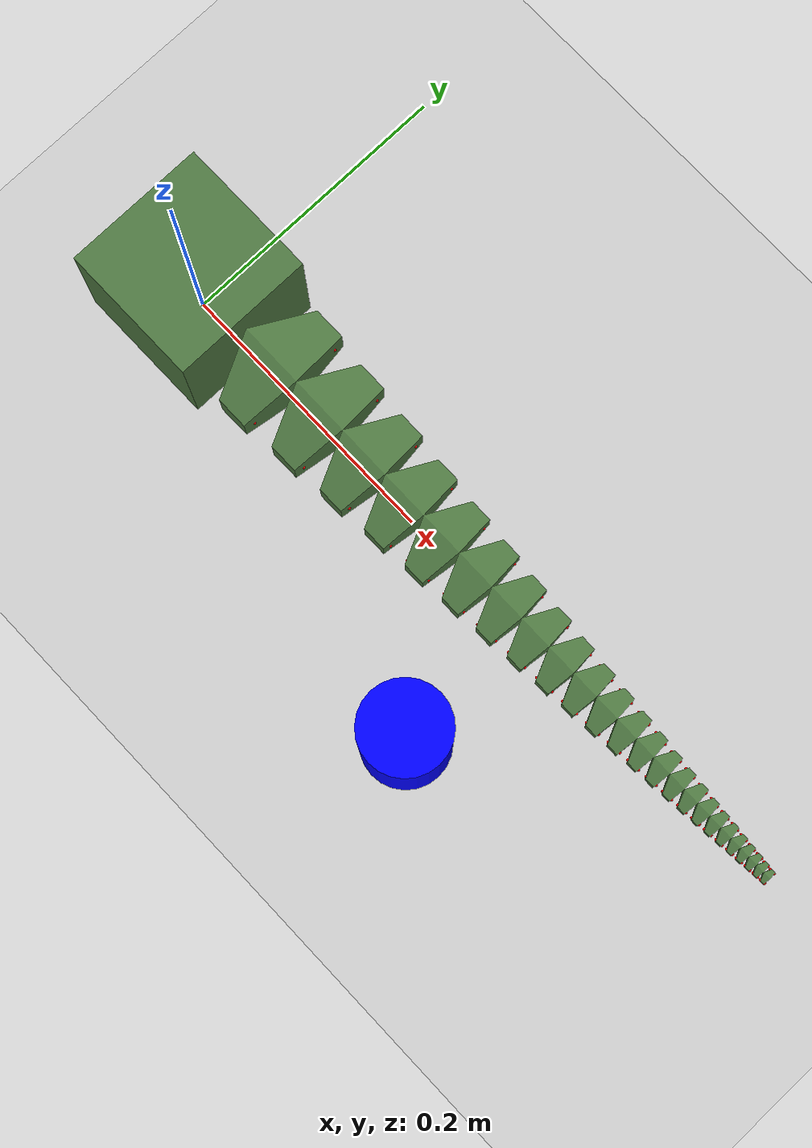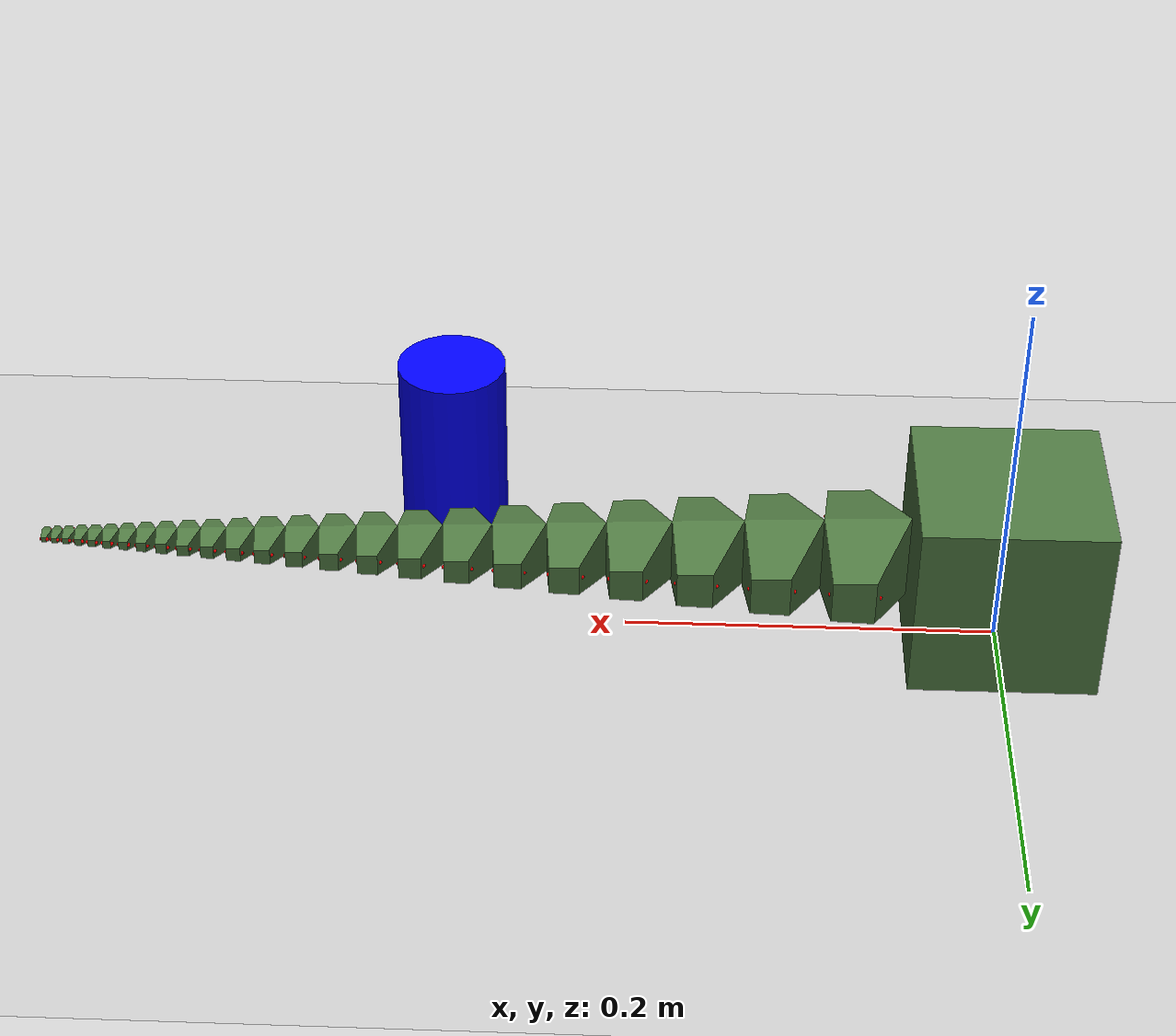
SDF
<?xml version="1.0" ?>
<sdf version="1.9">
  <world name="spirob">
    <physics name="1ms" type="dart">
      <max_step_size>0.001</max_step_size>
      <real_time_factor>1.0</real_time_factor>
      <real_time_update_rate>1000</real_time_update_rate>
      <max_contacts>20</max_contacts>
      <dart>
        <solver>
          <type>pgs</type>
        </solver>
        <collision_detector>bullet</collision_detector>
      </dart>
    </physics>

    <plugin name="gz::sim::systems::Physics"
      filename="gz-sim-physics-system">
    </plugin>
    <plugin name="gz::sim::systems::Sensors"
      filename="gz-sim-sensors-system">
      <render_engine>ogre2</render_engine>
    </plugin>
    <plugin name="gz::sim::systems::UserCommands"
      filename="gz-sim-user-commands-system">
    </plugin>
    <plugin name="gz::sim::systems::SceneBroadcaster"
      filename="gz-sim-scene-broadcaster-system">
    </plugin>
    <plugin name="gz::sim::systems::Imu"
      filename="gz-sim-imu-system">
    </plugin>

    <scene>
      <ambient>1.0 1.0 1.0</ambient>
      <background>0.8 0.8 0.8</background>
      <sky></sky>
    </scene>

    <light type="directional" name="sun">
      <cast_shadows>true</cast_shadows>
      <pose>0 0 10 0 0 0</pose>
      <diffuse>0.8 0.8 0.8 1</diffuse>
      <specular>0.8 0.8 0.8 1</specular>
      <attenuation>
        <range>1000</range>
        <constant>0.9</constant>
        <linear>0.01</linear>
        <quadratic>0.001</quadratic>
      </attenuation>
      <direction>-0.5 0.1 -0.9</direction>
    </light>

    <model name="ground_plane">
      <static>true</static>
      <link name="link">
        <collision name="collision">
          <geometry>
            <plane>
              <normal>0 0 1</normal>
              <size>100 100</size>
            </plane>
          </geometry>
        </collision>
        <visual name="visual">
          <geometry>
            <plane>
              <normal>0 0 1</normal>
              <size>100 100</size>
            </plane>
          </geometry>
          <material>
            <ambient>0.8 0.8 0.8</ambient>
            <diffuse>0.8 0.8 0.8</diffuse>
            <specular>0.1 0.1 0.1</specular>
          </material>
        </visual>
      </link>
    </model>

    <model name="arm">
      <static>0</static>
      <self_collide>1</self_collide>
      <include merge="true">
        <uri>model://spirob_arm</uri>
        <pose degrees="true">0 0 0.05 0 0 0</pose>
      </include>
      <joint name="arm_world" type="fixed">
        <parent>world</parent>
        <child>base_link</child>
      </joint>

    </model>

    <!-- cylinder target -->
    <model name="target">
      <static>true</static>
      <pose>0.3 -0.1 0.05 0 0 0</pose>
      <link name="base_link">
        <inertial auto="true" />
        <collision name="collision">
          <density>2000</density>
          <geometry>
            <cylinder>
              <radius>0.03</radius>
              <length>0.1</length>
            </cylinder>
          </geometry>
          <surface>
            <friction>
              <ode>
                <mu>1.0</mu>
                <mu2>1.0</mu2>
              </ode>
            </friction>
          </surface>
        </collision>
        <visual name="visual">
          <geometry>
            <cylinder>
              <radius>0.03</radius>
              <length>0.1</length>
            </cylinder>
          </geometry>
          <material>
            <ambient>0 0 1</ambient>
            <diffuse>0 0 1</diffuse>
            <specular>0.1 0.1 0.1</specular>
          </material>
        </visual>
      </link>
    </model>

  </world>
</sdf>

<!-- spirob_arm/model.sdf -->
<sdf version="1.9">
  <model name="spirob_arm">
    <static>0</static>
    <self_collide>1</self_collide>
    <link name="base_link">
      <pose degrees="true">0 0 0 0 0 0</pose>
      <inertial auto="true" />
      <collision name="collision">
        <pose degrees="true">0 0 0 0 0 0</pose>
        <density>10000</density>
        <geometry>
          <box>
            <size>0.1 0.1 0.1</size>
          </box>
        </geometry>
        <surface>
          <friction>
            <ode>
              <mu>1.0</mu>
              <mu2>1.0</mu2>
            </ode>
          </friction>
        </surface>
      </collision>
      <visual name="visual">
        <pose degrees="true">0 0 0 0 0 0</pose>
        <geometry>
          <box>
            <size>0.1 0.1 0.1</size>
          </box>
        </geometry>
        <material>
          <ambient>0.30859375 0.47265625 0.2578125</ambient>
          <diffuse>0.30859375 0.47265625 0.2578125</diffuse>
          <specular>0.1 0.1 0.1</specular>
        </material>
      </visual>
    </link>
    <joint name="joint01" type="fixed">
      <pose degrees="true" relative_to="base_link">0.05 0 0 0 0 0</pose>
      <parent>base_link</parent>
      <child>link1</child>
    </joint>

    <link name="link1">
      <pose degrees="true" relative_to="joint01">0 0 0 0 0 0</pose>
      <inertial auto="true" />
      <collision name="collision">
        <pose degrees="true">0 0 0 0 -90 180</pose>
        <density>1100</density>
        <geometry>
          <mesh>
            <scale>0.001000000 0.001000000 0.001000000</scale>
            <uri>meshes/baselink.stl</uri>
          </mesh>
        </geometry>
        <surface>
          <friction>
            <ode>
              <mu>1.0</mu>
              <mu2>1.0</mu2>
            </ode>
          </friction>
        </surface>
      </collision>
      <visual name="visual">
        <pose degrees="true">0 0 0 0 -90 180</pose>
        <geometry>
          <mesh>
            <scale>0.001000000 0.001000000 0.001000000</scale>
            <uri>meshes/baselink.stl</uri>
          </mesh>
        </geometry>
        <material>
          <ambient>0.30859375 0.47265625 0.2578125</ambient>
          <diffuse>0.30859375 0.47265625 0.2578125</diffuse>
          <specular>0.1 0.1 0.1</specular>
        </material>
      </visual>
      <visual name="s1_1">
        <pose>0.016795002 0.036394210 0 0 0 0</pose>
        <geometry>
          <sphere>
            <radius>0.001000</radius>
          </sphere>
        </geometry>
        <material>
          <ambient>1 0 0</ambient>
          <diffuse>1 0 0</diffuse>
          <specular>0.1 0.1 0.1</specular>
        </material>
      </visual>
      <visual name="s1_2">
        <pose>0.042801474 0.034423562 0 0 0 0</pose>
        <geometry>
          <sphere>
            <radius>0.001000</radius>
          </sphere>
        </geometry>
        <material>
          <ambient>1 0 0</ambient>
          <diffuse>1 0 0</diffuse>
          <specular>0.1 0.1 0.1</specular>
        </material>
      </visual>
      <visual name="s1_3">
        <pose>0.016795002 -0.036394210 0 0 0 0</pose>
        <geometry>
          <sphere>
            <radius>0.001000</radius>
          </sphere>
        </geometry>
        <material>
          <ambient>1 0 0</ambient>
          <diffuse>1 0 0</diffuse>
          <specular>0.1 0.1 0.1</specular>
        </material>
      </visual>
      <visual name="s1_4">
        <pose>0.042801474 -0.034423562 0 0 0 0</pose>
        <geometry>
          <sphere>
            <radius>0.001000</radius>
          </sphere>
        </geometry>
        <material>
          <ambient>1 0 0</ambient>
          <diffuse>1 0 0</diffuse>
          <specular>0.1 0.1 0.1</specular>
        </material>
      </visual>
    </link>
    <link name="link2">
      <pose degrees="true" relative_to="joint12">0 0 0 0 0 0</pose>
      <inertial auto="true" />
      <collision name="collision">
        <density>1100</density>
        <pose degrees="true">0 0 0 0 -90 180</pose>
        <geometry>
          <mesh>
            <scale>0.000911774 0.000911774 0.000911774</scale>
            <uri>meshes/baselink.stl</uri>
          </mesh>
        </geometry>
        <surface>
          <friction>
            <ode>
              <mu>1.0</mu>
              <mu2>1.0</mu2>
            </ode>
          </friction>
        </surface>
      </collision>
      <visual name="visual">
        <pose degrees="true">0 0 0 0 -90 180</pose>
        <geometry>
          <mesh>
            <scale>0.000911774 0.000911774 0.000911774</scale>
            <uri>meshes/baselink.stl</uri>
          </mesh>
        </geometry>
        <material>
          <ambient>0.30859375 0.47265625 0.2578125</ambient>
          <diffuse>0.30859375 0.47265625 0.2578125</diffuse>
          <specular>0.1 0.1 0.1</specular>
        </material>
      </visual>
      <visual name="s2_1">
        <pose>0.015313251 0.033183304 0 0 0 0</pose>
        <geometry>
          <sphere>
            <radius>0.001000</radius>
          </sphere>
        </geometry>
        <material>
          <ambient>1 0 0</ambient>
          <diffuse>1 0 0</diffuse>
          <specular>0.1 0.1 0.1</specular>
        </material>
      </visual>
      <visual name="s2_2">
        <pose>0.039025283 0.031386518 0 0 0 0</pose>
        <geometry>
          <sphere>
            <radius>0.001000</radius>
          </sphere>
        </geometry>
        <material>
          <ambient>1 0 0</ambient>
          <diffuse>1 0 0</diffuse>
          <specular>0.1 0.1 0.1</specular>
        </material>
      </visual>
      <visual name="s2_3">
        <pose>0.015313251 -0.033183304 0 0 0 0</pose>
        <geometry>
          <sphere>
            <radius>0.001000</radius>
          </sphere>
        </geometry>
        <material>
          <ambient>1 0 0</ambient>
          <diffuse>1 0 0</diffuse>
          <specular>0.1 0.1 0.1</specular>
        </material>
      </visual>
      <visual name="s2_4">
        <pose>0.039025283 -0.031386518 0 0 0 0</pose>
        <geometry>
          <sphere>
            <radius>0.001000</radius>
          </sphere>
        </geometry>
        <material>
          <ambient>1 0 0</ambient>
          <diffuse>1 0 0</diffuse>
          <specular>0.1 0.1 0.1</specular>
        </material>
      </visual>
    </link>
    <link name="link3">
      <pose degrees="true" relative_to="joint23">0 0 0 0 0 0</pose>
      <inertial auto="true" />
      <collision name="collision">
        <pose degrees="true">0 0 0 0 -90 180</pose>
        <density>1100</density>
        <geometry>
          <mesh>
            <scale>0.000831332 0.000831332 0.000831332</scale>
            <uri>meshes/baselink.stl</uri>
          </mesh>
        </geometry>
        <surface>
          <friction>
            <ode>
              <mu>1.0</mu>
              <mu2>1.0</mu2>
            </ode>
          </friction>
        </surface>
      </collision>
      <visual name="visual">
        <pose degrees="true">0 0 0 0 -90 180</pose>
        <geometry>
          <mesh>
            <scale>0.000831332 0.000831332 0.000831332</scale>
            <uri>meshes/baselink.stl</uri>
          </mesh>
        </geometry>
        <material>
          <ambient>0.30859375 0.47265625 0.2578125</ambient>
          <diffuse>0.30859375 0.47265625 0.2578125</diffuse>
          <specular>0.1 0.1 0.1</specular>
        </material>
      </visual>
      <visual name="s3_1">
        <pose>0.013962228 0.030255683 0 0 0 0</pose>
        <geometry>
          <sphere>
            <radius>0.001000</radius>
          </sphere>
        </geometry>
        <material>
          <ambient>1 0 0</ambient>
          <diffuse>1 0 0</diffuse>
          <specular>0.1 0.1 0.1</specular>
        </material>
      </visual>
      <visual name="s3_2">
        <pose>0.035582249 0.028617420 0 0 0 0</pose>
        <geometry>
          <sphere>
            <radius>0.001000</radius>
          </sphere>
        </geometry>
        <material>
          <ambient>1 0 0</ambient>
          <diffuse>1 0 0</diffuse>
          <specular>0.1 0.1 0.1</specular>
        </material>
      </visual>
      <visual name="s3_3">
        <pose>0.013962228 -0.030255683 0 0 0 0</pose>
        <geometry>
          <sphere>
            <radius>0.001000</radius>
          </sphere>
        </geometry>
        <material>
          <ambient>1 0 0</ambient>
          <diffuse>1 0 0</diffuse>
          <specular>0.1 0.1 0.1</specular>
        </material>
      </visual>
      <visual name="s3_4">
        <pose>0.035582249 -0.028617420 0 0 0 0</pose>
        <geometry>
          <sphere>
            <radius>0.001000</radius>
          </sphere>
        </geometry>
        <material>
          <ambient>1 0 0</ambient>
          <diffuse>1 0 0</diffuse>
          <specular>0.1 0.1 0.1</specular>
        </material>
      </visual>
    </link>
    <link name="link4">
      <pose degrees="true" relative_to="joint34">0 0 0 0 0 0</pose>
      <inertial auto="true" />
      <collision name="collision">
        <pose degrees="true">0 0 0 0 -90 180</pose>
        <density>1100</density>
        <geometry>
          <mesh>
            <scale>0.000757987 0.000757987 0.000757987</scale>
            <uri>meshes/baselink.stl</uri>
          </mesh>
        </geometry>
        <surface>
          <friction>
            <ode>
              <mu>1.0</mu>
              <mu2>1.0</mu2>
            </ode>
          </friction>
        </surface>
      </collision>
      <visual name="visual">
        <pose degrees="true">0 0 0 0 -90 180</pose>
        <geometry>
          <mesh>
            <scale>0.000757987 0.000757987 0.000757987</scale>
            <uri>meshes/baselink.stl</uri>
          </mesh>
        </geometry>
        <material>
          <ambient>0.30859375 0.47265625 0.2578125</ambient>
          <diffuse>0.30859375 0.47265625 0.2578125</diffuse>
          <specular>0.1 0.1 0.1</specular>
        </material>
      </visual>
      <visual name="s4_1">
        <pose>0.012730400 0.027586354 0 0 0 0</pose>
        <geometry>
          <sphere>
            <radius>0.001000</radius>
          </sphere>
        </geometry>
        <material>
          <ambient>1 0 0</ambient>
          <diffuse>1 0 0</diffuse>
          <specular>0.1 0.1 0.1</specular>
        </material>
      </visual>
      <visual name="s4_2">
        <pose>0.032442980 0.026092627 0 0 0 0</pose>
        <geometry>
          <sphere>
            <radius>0.001000</radius>
          </sphere>
        </geometry>
        <material>
          <ambient>1 0 0</ambient>
          <diffuse>1 0 0</diffuse>
          <specular>0.1 0.1 0.1</specular>
        </material>
      </visual>
      <visual name="s4_3">
        <pose>0.012730400 -0.027586354 0 0 0 0</pose>
        <geometry>
          <sphere>
            <radius>0.001000</radius>
          </sphere>
        </geometry>
        <material>
          <ambient>1 0 0</ambient>
          <diffuse>1 0 0</diffuse>
          <specular>0.1 0.1 0.1</specular>
        </material>
      </visual>
      <visual name="s4_4">
        <pose>0.032442980 -0.026092627 0 0 0 0</pose>
        <geometry>
          <sphere>
            <radius>0.001000</radius>
          </sphere>
        </geometry>
        <material>
          <ambient>1 0 0</ambient>
          <diffuse>1 0 0</diffuse>
          <specular>0.1 0.1 0.1</specular>
        </material>
      </visual>
    </link>
    <link name="link5">
      <pose degrees="true" relative_to="joint45">0 0 0 0 0 0</pose>
      <inertial auto="true" />
      <collision name="collision">
        <pose degrees="true">0 0 0 0 -90 180</pose>
        <density>1100</density>
        <geometry>
          <mesh>
            <scale>0.000691113 0.000691113 0.000691113</scale>
            <uri>meshes/baselink.stl</uri>
          </mesh>
        </geometry>
        <surface>
          <friction>
            <ode>
              <mu>1.0</mu>
              <mu2>1.0</mu2>
            </ode>
          </friction>
        </surface>
      </collision>
      <visual name="visual">
        <pose degrees="true">0 0 0 0 -90 180</pose>
        <geometry>
          <mesh>
            <scale>0.000691113 0.000691113 0.000691113</scale>
            <uri>meshes/baselink.stl</uri>
          </mesh>
        </geometry>
        <material>
          <ambient>0.30859375 0.47265625 0.2578125</ambient>
          <diffuse>0.30859375 0.47265625 0.2578125</diffuse>
          <specular>0.1 0.1 0.1</specular>
        </material>
      </visual>
      <visual name="s5_1">
        <pose>0.011607252 0.025152528 0 0 0 0</pose>
        <geometry>
          <sphere>
            <radius>0.001000</radius>
          </sphere>
        </geometry>
        <material>
          <ambient>1 0 0</ambient>
          <diffuse>1 0 0</diffuse>
          <specular>0.1 0.1 0.1</specular>
        </material>
      </visual>
      <visual name="s5_2">
        <pose>0.029580674 0.023790586 0 0 0 0</pose>
        <geometry>
          <sphere>
            <radius>0.001000</radius>
          </sphere>
        </geometry>
        <material>
          <ambient>1 0 0</ambient>
          <diffuse>1 0 0</diffuse>
          <specular>0.1 0.1 0.1</specular>
        </material>
      </visual>
      <visual name="s5_3">
        <pose>0.011607252 -0.025152528 0 0 0 0</pose>
        <geometry>
          <sphere>
            <radius>0.001000</radius>
          </sphere>
        </geometry>
        <material>
          <ambient>1 0 0</ambient>
          <diffuse>1 0 0</diffuse>
          <specular>0.1 0.1 0.1</specular>
        </material>
      </visual>
      <visual name="s5_4">
        <pose>0.029580674 -0.023790586 0 0 0 0</pose>
        <geometry>
          <sphere>
            <radius>0.001000</radius>
          </sphere>
        </geometry>
        <material>
          <ambient>1 0 0</ambient>
          <diffuse>1 0 0</diffuse>
          <specular>0.1 0.1 0.1</specular>
        </material>
      </visual>
    </link>
    <link name="link6">
      <pose degrees="true" relative_to="joint56">0 0 0 0 0 0</pose>
      <inertial auto="true" />
      <collision name="collision">
        <pose degrees="true">0 0 0 0 -90 180</pose>
        <density>1100</density>
        <geometry>
          <mesh>
            <scale>0.000630139 0.000630139 0.000630139</scale>
            <uri>meshes/baselink.stl</uri>
          </mesh>
        </geometry>
        <surface>
          <friction>
            <ode>
              <mu>1.0</mu>
              <mu2>1.0</mu2>
            </ode>
          </friction>
        </surface>
      </collision>
      <visual name="visual">
        <pose degrees="true">0 0 0 0 -90 180</pose>
        <geometry>
          <mesh>
            <scale>0.000630139 0.000630139 0.000630139</scale>
            <uri>meshes/baselink.stl</uri>
          </mesh>
        </geometry>
        <material>
          <ambient>0.30859375 0.47265625 0.2578125</ambient>
          <diffuse>0.30859375 0.47265625 0.2578125</diffuse>
          <specular>0.1 0.1 0.1</specular>
        </material>
      </visual>
      <visual name="s6_1">
        <pose>0.010583193 0.022933428 0 0 0 0</pose>
        <geometry>
          <sphere>
            <radius>0.001000</radius>
          </sphere>
        </geometry>
        <material>
          <ambient>1 0 0</ambient>
          <diffuse>1 0 0</diffuse>
          <specular>0.1 0.1 0.1</specular>
        </material>
      </visual>
      <visual name="s6_2">
        <pose>0.026970898 0.021691645 0 0 0 0</pose>
        <geometry>
          <sphere>
            <radius>0.001000</radius>
          </sphere>
        </geometry>
        <material>
          <ambient>1 0 0</ambient>
          <diffuse>1 0 0</diffuse>
          <specular>0.1 0.1 0.1</specular>
        </material>
      </visual>
      <visual name="s6_3">
        <pose>0.010583193 -0.022933428 0 0 0 0</pose>
        <geometry>
          <sphere>
            <radius>0.001000</radius>
          </sphere>
        </geometry>
        <material>
          <ambient>1 0 0</ambient>
          <diffuse>1 0 0</diffuse>
          <specular>0.1 0.1 0.1</specular>
        </material>
      </visual>
      <visual name="s6_4">
        <pose>0.026970898 -0.021691645 0 0 0 0</pose>
        <geometry>
          <sphere>
            <radius>0.001000</radius>
          </sphere>
        </geometry>
        <material>
          <ambient>1 0 0</ambient>
          <diffuse>1 0 0</diffuse>
          <specular>0.1 0.1 0.1</specular>
        </material>
      </visual>
    </link>
    <link name="link7">
      <pose degrees="true" relative_to="joint67">0 0 0 0 0 0</pose>
      <inertial auto="true" />
      <collision name="collision">
        <pose degrees="true">0 0 0 0 -90 180</pose>
        <density>1100</density>
        <geometry>
          <mesh>
            <scale>0.000574545 0.000574545 0.000574545</scale>
            <uri>meshes/baselink.stl</uri>
          </mesh>
        </geometry>
        <surface>
          <friction>
            <ode>
              <mu>1.0</mu>
              <mu2>1.0</mu2>
            </ode>
          </friction>
        </surface>
      </collision>
      <visual name="visual">
        <pose degrees="true">0 0 0 0 -90 180</pose>
        <geometry>
          <mesh>
            <scale>0.000574545 0.000574545 0.000574545</scale>
            <uri>meshes/baselink.stl</uri>
          </mesh>
        </geometry>
        <material>
          <ambient>0.30859375 0.47265625 0.2578125</ambient>
          <diffuse>0.30859375 0.47265625 0.2578125</diffuse>
          <specular>0.1 0.1 0.1</specular>
        </material>
      </visual>
      <visual name="s7_1">
        <pose>0.009649483 0.020910109 0 0 0 0</pose>
        <geometry>
          <sphere>
            <radius>0.001000</radius>
          </sphere>
        </geometry>
        <material>
          <ambient>1 0 0</ambient>
          <diffuse>1 0 0</diffuse>
          <specular>0.1 0.1 0.1</specular>
        </material>
      </visual>
      <visual name="s7_2">
        <pose>0.024591371 0.019777884 0 0 0 0</pose>
        <geometry>
          <sphere>
            <radius>0.001000</radius>
          </sphere>
        </geometry>
        <material>
          <ambient>1 0 0</ambient>
          <diffuse>1 0 0</diffuse>
          <specular>0.1 0.1 0.1</specular>
        </material>
      </visual>
      <visual name="s7_3">
        <pose>0.009649483 -0.020910109 0 0 0 0</pose>
        <geometry>
          <sphere>
            <radius>0.001000</radius>
          </sphere>
        </geometry>
        <material>
          <ambient>1 0 0</ambient>
          <diffuse>1 0 0</diffuse>
          <specular>0.1 0.1 0.1</specular>
        </material>
      </visual>
      <visual name="s7_4">
        <pose>0.024591371 -0.019777884 0 0 0 0</pose>
        <geometry>
          <sphere>
            <radius>0.001000</radius>
          </sphere>
        </geometry>
        <material>
          <ambient>1 0 0</ambient>
          <diffuse>1 0 0</diffuse>
          <specular>0.1 0.1 0.1</specular>
        </material>
      </visual>
    </link>
    <link name="link8">
      <pose degrees="true" relative_to="joint78">0 0 0 0 0 0</pose>
      <inertial auto="true" />
      <collision name="collision">
        <pose degrees="true">0 0 0 0 -90 180</pose>
        <density>1100</density>
        <geometry>
          <mesh>
            <scale>0.000523855 0.000523855 0.000523855</scale>
            <uri>meshes/baselink.stl</uri>
          </mesh>
        </geometry>
        <surface>
          <friction>
            <ode>
              <mu>1.0</mu>
              <mu2>1.0</mu2>
            </ode>
          </friction>
        </surface>
      </collision>
      <visual name="visual">
        <pose degrees="true">0 0 0 0 -90 180</pose>
        <geometry>
          <mesh>
            <scale>0.000523855 0.000523855 0.000523855</scale>
            <uri>meshes/baselink.stl</uri>
          </mesh>
        </geometry>
        <material>
          <ambient>0.30859375 0.47265625 0.2578125</ambient>
          <diffuse>0.30859375 0.47265625 0.2578125</diffuse>
          <specular>0.1 0.1 0.1</specular>
        </material>
      </visual>
      <visual name="s8_1">
        <pose>0.008798151 0.019065300 0 0 0 0</pose>
        <geometry>
          <sphere>
            <radius>0.001000</radius>
          </sphere>
        </geometry>
        <material>
          <ambient>1 0 0</ambient>
          <diffuse>1 0 0</diffuse>
          <specular>0.1 0.1 0.1</specular>
        </material>
      </visual>
      <visual name="s8_2">
        <pose>0.022421779 0.018032965 0 0 0 0</pose>
        <geometry>
          <sphere>
            <radius>0.001000</radius>
          </sphere>
        </geometry>
        <material>
          <ambient>1 0 0</ambient>
          <diffuse>1 0 0</diffuse>
          <specular>0.1 0.1 0.1</specular>
        </material>
      </visual>
      <visual name="s8_3">
        <pose>0.008798151 -0.019065300 0 0 0 0</pose>
        <geometry>
          <sphere>
            <radius>0.001000</radius>
          </sphere>
        </geometry>
        <material>
          <ambient>1 0 0</ambient>
          <diffuse>1 0 0</diffuse>
          <specular>0.1 0.1 0.1</specular>
        </material>
      </visual>
      <visual name="s8_4">
        <pose>0.022421779 -0.018032965 0 0 0 0</pose>
        <geometry>
          <sphere>
            <radius>0.001000</radius>
          </sphere>
        </geometry>
        <material>
          <ambient>1 0 0</ambient>
          <diffuse>1 0 0</diffuse>
          <specular>0.1 0.1 0.1</specular>
        </material>
      </visual>
    </link>
    <link name="link9">
      <pose degrees="true" relative_to="joint89">0 0 0 0 0 0</pose>
      <inertial auto="true" />
      <collision name="collision">
        <pose degrees="true">0 0 0 0 -90 180</pose>
        <density>1100</density>
        <geometry>
          <mesh>
            <scale>0.000477638 0.000477638 0.000477638</scale>
            <uri>meshes/baselink.stl</uri>
          </mesh>
        </geometry>
        <surface>
          <friction>
            <ode>
              <mu>1.0</mu>
              <mu2>1.0</mu2>
            </ode>
          </friction>
        </surface>
      </collision>
      <visual name="visual">
        <pose degrees="true">0 0 0 0 -90 180</pose>
        <geometry>
          <mesh>
            <scale>0.000477638 0.000477638 0.000477638</scale>
            <uri>meshes/baselink.stl</uri>
          </mesh>
        </geometry>
        <material>
          <ambient>0.30859375 0.47265625 0.2578125</ambient>
          <diffuse>0.30859375 0.47265625 0.2578125</diffuse>
          <specular>0.1 0.1 0.1</specular>
        </material>
      </visual>
      <visual name="s9_1">
        <pose>0.008021928 0.017383250 0 0 0 0</pose>
        <geometry>
          <sphere>
            <radius>0.001000</radius>
          </sphere>
        </geometry>
        <material>
          <ambient>1 0 0</ambient>
          <diffuse>1 0 0</diffuse>
          <specular>0.1 0.1 0.1</specular>
        </material>
      </visual>
      <visual name="s9_2">
        <pose>0.020443602 0.016441994 0 0 0 0</pose>
        <geometry>
          <sphere>
            <radius>0.001000</radius>
          </sphere>
        </geometry>
        <material>
          <ambient>1 0 0</ambient>
          <diffuse>1 0 0</diffuse>
          <specular>0.1 0.1 0.1</specular>
        </material>
      </visual>
      <visual name="s9_3">
        <pose>0.008021928 -0.017383250 0 0 0 0</pose>
        <geometry>
          <sphere>
            <radius>0.001000</radius>
          </sphere>
        </geometry>
        <material>
          <ambient>1 0 0</ambient>
          <diffuse>1 0 0</diffuse>
          <specular>0.1 0.1 0.1</specular>
        </material>
      </visual>
      <visual name="s9_4">
        <pose>0.020443602 -0.016441994 0 0 0 0</pose>
        <geometry>
          <sphere>
            <radius>0.001000</radius>
          </sphere>
        </geometry>
        <material>
          <ambient>1 0 0</ambient>
          <diffuse>1 0 0</diffuse>
          <specular>0.1 0.1 0.1</specular>
        </material>
      </visual>
    </link>
    <link name="link10">
      <pose degrees="true" relative_to="joint910">0 0 0 0 0 0</pose>
      <inertial auto="true" />
      <collision name="collision">
        <pose degrees="true">0 0 0 0 -90 180</pose>
        <density>1100</density>
        <geometry>
          <mesh>
            <scale>0.000435498 0.000435498 0.000435498</scale>
            <uri>meshes/baselink.stl</uri>
          </mesh>
        </geometry>
        <surface>
          <friction>
            <ode>
              <mu>1.0</mu>
              <mu2>1.0</mu2>
            </ode>
          </friction>
        </surface>
      </collision>
      <visual name="visual">
        <pose degrees="true">0 0 0 0 -90 180</pose>
        <geometry>
          <mesh>
            <scale>0.000435498 0.000435498 0.000435498</scale>
            <uri>meshes/baselink.stl</uri>
          </mesh>
        </geometry>
        <material>
          <ambient>0.30859375 0.47265625 0.2578125</ambient>
          <diffuse>0.30859375 0.47265625 0.2578125</diffuse>
          <specular>0.1 0.1 0.1</specular>
        </material>
      </visual>
      <visual name="s10_1">
        <pose>0.007314187 0.015849600 0 0 0 0</pose>
        <geometry>
          <sphere>
            <radius>0.001000</radius>
          </sphere>
        </geometry>
        <material>
          <ambient>1 0 0</ambient>
          <diffuse>1 0 0</diffuse>
          <specular>0.1 0.1 0.1</specular>
        </material>
      </visual>
      <visual name="s10_2">
        <pose>0.018639950 0.014991387 0 0 0 0</pose>
        <geometry>
          <sphere>
            <radius>0.001000</radius>
          </sphere>
        </geometry>
        <material>
          <ambient>1 0 0</ambient>
          <diffuse>1 0 0</diffuse>
          <specular>0.1 0.1 0.1</specular>
        </material>
      </visual>
      <visual name="s10_3">
        <pose>0.007314187 -0.015849600 0 0 0 0</pose>
        <geometry>
          <sphere>
            <radius>0.001000</radius>
          </sphere>
        </geometry>
        <material>
          <ambient>1 0 0</ambient>
          <diffuse>1 0 0</diffuse>
          <specular>0.1 0.1 0.1</specular>
        </material>
      </visual>
      <visual name="s10_4">
        <pose>0.018639950 -0.014991387 0 0 0 0</pose>
        <geometry>
          <sphere>
            <radius>0.001000</radius>
          </sphere>
        </geometry>
        <material>
          <ambient>1 0 0</ambient>
          <diffuse>1 0 0</diffuse>
          <specular>0.1 0.1 0.1</specular>
        </material>
      </visual>
    </link>
    <link name="link11">
      <pose degrees="true" relative_to="joint1011">0 0 0 0 0 0</pose>
      <inertial auto="true" />
      <collision name="collision">
        <pose degrees="true">0 0 0 0 -90 180</pose>
        <density>1100</density>
        <geometry>
          <mesh>
            <scale>0.000397076 0.000397076 0.000397076</scale>
            <uri>meshes/baselink.stl</uri>
          </mesh>
        </geometry>
        <surface>
          <friction>
            <ode>
              <mu>1.0</mu>
              <mu2>1.0</mu2>
            </ode>
          </friction>
        </surface>
      </collision>
      <visual name="visual">
        <pose degrees="true">0 0 0 0 -90 180</pose>
        <geometry>
          <mesh>
            <scale>0.000397076 0.000397076 0.000397076</scale>
            <uri>meshes/baselink.stl</uri>
          </mesh>
        </geometry>
        <material>
          <ambient>0.30859375 0.47265625 0.2578125</ambient>
          <diffuse>0.30859375 0.47265625 0.2578125</diffuse>
          <specular>0.1 0.1 0.1</specular>
        </material>
      </visual>
      <visual name="s11_1">
        <pose>0.006668888 0.014451258 0 0 0 0</pose>
        <geometry>
          <sphere>
            <radius>0.001000</radius>
          </sphere>
        </geometry>
        <material>
          <ambient>1 0 0</ambient>
          <diffuse>1 0 0</diffuse>
          <specular>0.1 0.1 0.1</specular>
        </material>
      </visual>
      <visual name="s11_2">
        <pose>0.016995427 0.013668761 0 0 0 0</pose>
        <geometry>
          <sphere>
            <radius>0.001000</radius>
          </sphere>
        </geometry>
        <material>
          <ambient>1 0 0</ambient>
          <diffuse>1 0 0</diffuse>
          <specular>0.1 0.1 0.1</specular>
        </material>
      </visual>
      <visual name="s11_3">
        <pose>0.006668888 -0.014451258 0 0 0 0</pose>
        <geometry>
          <sphere>
            <radius>0.001000</radius>
          </sphere>
        </geometry>
        <material>
          <ambient>1 0 0</ambient>
          <diffuse>1 0 0</diffuse>
          <specular>0.1 0.1 0.1</specular>
        </material>
      </visual>
      <visual name="s11_4">
        <pose>0.016995427 -0.013668761 0 0 0 0</pose>
        <geometry>
          <sphere>
            <radius>0.001000</radius>
          </sphere>
        </geometry>
        <material>
          <ambient>1 0 0</ambient>
          <diffuse>1 0 0</diffuse>
          <specular>0.1 0.1 0.1</specular>
        </material>
      </visual>
    </link>
    <link name="link12">
      <pose degrees="true" relative_to="joint1112">0 0 0 0 0 0</pose>
      <inertial auto="true" />
      <collision name="collision">
        <pose degrees="true">0 0 0 0 -90 180</pose>
        <density>1100</density>
        <geometry>
          <mesh>
            <scale>0.000362043 0.000362043 0.000362043</scale>
            <uri>meshes/baselink.stl</uri>
          </mesh>
        </geometry>
        <surface>
          <friction>
            <ode>
              <mu>1.0</mu>
              <mu2>1.0</mu2>
            </ode>
          </friction>
        </surface>
      </collision>
      <visual name="visual">
        <pose degrees="true">0 0 0 0 -90 180</pose>
        <geometry>
          <mesh>
            <scale>0.000362043 0.000362043 0.000362043</scale>
            <uri>meshes/baselink.stl</uri>
          </mesh>
        </geometry>
        <material>
          <ambient>0.30859375 0.47265625 0.2578125</ambient>
          <diffuse>0.30859375 0.47265625 0.2578125</diffuse>
          <specular>0.1 0.1 0.1</specular>
        </material>
      </visual>
      <visual name="s12_1">
        <pose>0.006080520 0.013176285 0 0 0 0</pose>
        <geometry>
          <sphere>
            <radius>0.001000</radius>
          </sphere>
        </geometry>
        <material>
          <ambient>1 0 0</ambient>
          <diffuse>1 0 0</diffuse>
          <specular>0.1 0.1 0.1</specular>
        </material>
      </visual>
      <visual name="s12_2">
        <pose>0.015495993 0.012462825 0 0 0 0</pose>
        <geometry>
          <sphere>
            <radius>0.001000</radius>
          </sphere>
        </geometry>
        <material>
          <ambient>1 0 0</ambient>
          <diffuse>1 0 0</diffuse>
          <specular>0.1 0.1 0.1</specular>
        </material>
      </visual>
      <visual name="s12_3">
        <pose>0.006080520 -0.013176285 0 0 0 0</pose>
        <geometry>
          <sphere>
            <radius>0.001000</radius>
          </sphere>
        </geometry>
        <material>
          <ambient>1 0 0</ambient>
          <diffuse>1 0 0</diffuse>
          <specular>0.1 0.1 0.1</specular>
        </material>
      </visual>
      <visual name="s12_4">
        <pose>0.015495993 -0.012462825 0 0 0 0</pose>
        <geometry>
          <sphere>
            <radius>0.001000</radius>
          </sphere>
        </geometry>
        <material>
          <ambient>1 0 0</ambient>
          <diffuse>1 0 0</diffuse>
          <specular>0.1 0.1 0.1</specular>
        </material>
      </visual>
    </link>
    <link name="link13">
      <pose degrees="true" relative_to="joint1213">0 0 0 0 0 0</pose>
      <inertial auto="true" />
      <collision name="collision">
        <pose degrees="true">0 0 0 0 -90 180</pose>
        <density>1100</density>
        <geometry>
          <mesh>
            <scale>0.000330102 0.000330102 0.000330102</scale>
            <uri>meshes/baselink.stl</uri>
          </mesh>
        </geometry>
        <surface>
          <friction>
            <ode>
              <mu>1.0</mu>
              <mu2>1.0</mu2>
            </ode>
          </friction>
        </surface>
      </collision>
      <visual name="visual">
        <pose degrees="true">0 0 0 0 -90 180</pose>
        <geometry>
          <mesh>
            <scale>0.000330102 0.000330102 0.000330102</scale>
            <uri>meshes/baselink.stl</uri>
          </mesh>
        </geometry>
        <material>
          <ambient>0.30859375 0.47265625 0.2578125</ambient>
          <diffuse>0.30859375 0.47265625 0.2578125</diffuse>
          <specular>0.1 0.1 0.1</specular>
        </material>
      </visual>
      <visual name="s13_1">
        <pose>0.005544062 0.012013798 0 0 0 0</pose>
        <geometry>
          <sphere>
            <radius>0.001000</radius>
          </sphere>
        </geometry>
        <material>
          <ambient>1 0 0</ambient>
          <diffuse>1 0 0</diffuse>
          <specular>0.1 0.1 0.1</specular>
        </material>
      </visual>
      <visual name="s13_2">
        <pose>0.014128848 0.011363283 0 0 0 0</pose>
        <geometry>
          <sphere>
            <radius>0.001000</radius>
          </sphere>
        </geometry>
        <material>
          <ambient>1 0 0</ambient>
          <diffuse>1 0 0</diffuse>
          <specular>0.1 0.1 0.1</specular>
        </material>
      </visual>
      <visual name="s13_3">
        <pose>0.005544062 -0.012013798 0 0 0 0</pose>
        <geometry>
          <sphere>
            <radius>0.001000</radius>
          </sphere>
        </geometry>
        <material>
          <ambient>1 0 0</ambient>
          <diffuse>1 0 0</diffuse>
          <specular>0.1 0.1 0.1</specular>
        </material>
      </visual>
      <visual name="s13_4">
        <pose>0.014128848 -0.011363283 0 0 0 0</pose>
        <geometry>
          <sphere>
            <radius>0.001000</radius>
          </sphere>
        </geometry>
        <material>
          <ambient>1 0 0</ambient>
          <diffuse>1 0 0</diffuse>
          <specular>0.1 0.1 0.1</specular>
        </material>
      </visual>
    </link>
    <link name="link14">
      <pose degrees="true" relative_to="joint1314">0 0 0 0 0 0</pose>
      <inertial auto="true" />
      <collision name="collision">
        <pose degrees="true">0 0 0 0 -90 180</pose>
        <density>1100</density>
        <geometry>
          <mesh>
            <scale>0.000300978 0.000300978 0.000300978</scale>
            <uri>meshes/baselink.stl</uri>
          </mesh>
        </geometry>
        <surface>
          <friction>
            <ode>
              <mu>1.0</mu>
              <mu2>1.0</mu2>
            </ode>
          </friction>
        </surface>
      </collision>
      <visual name="visual">
        <pose degrees="true">0 0 0 0 -90 180</pose>
        <geometry>
          <mesh>
            <scale>0.000300978 0.000300978 0.000300978</scale>
            <uri>meshes/baselink.stl</uri>
          </mesh>
        </geometry>
        <material>
          <ambient>0.30859375 0.47265625 0.2578125</ambient>
          <diffuse>0.30859375 0.47265625 0.2578125</diffuse>
          <specular>0.1 0.1 0.1</specular>
        </material>
      </visual>
      <visual name="s14_1">
        <pose>0.005054933 0.010953872 0 0 0 0</pose>
        <geometry>
          <sphere>
            <radius>0.001000</radius>
          </sphere>
        </geometry>
        <material>
          <ambient>1 0 0</ambient>
          <diffuse>1 0 0</diffuse>
          <specular>0.1 0.1 0.1</specular>
        </material>
      </visual>
      <visual name="s14_2">
        <pose>0.012882320 0.010360749 0 0 0 0</pose>
        <geometry>
          <sphere>
            <radius>0.001000</radius>
          </sphere>
        </geometry>
        <material>
          <ambient>1 0 0</ambient>
          <diffuse>1 0 0</diffuse>
          <specular>0.1 0.1 0.1</specular>
        </material>
      </visual>
      <visual name="s14_3">
        <pose>0.005054933 -0.010953872 0 0 0 0</pose>
        <geometry>
          <sphere>
            <radius>0.001000</radius>
          </sphere>
        </geometry>
        <material>
          <ambient>1 0 0</ambient>
          <diffuse>1 0 0</diffuse>
          <specular>0.1 0.1 0.1</specular>
        </material>
      </visual>
      <visual name="s14_4">
        <pose>0.012882320 -0.010360749 0 0 0 0</pose>
        <geometry>
          <sphere>
            <radius>0.001000</radius>
          </sphere>
        </geometry>
        <material>
          <ambient>1 0 0</ambient>
          <diffuse>1 0 0</diffuse>
          <specular>0.1 0.1 0.1</specular>
        </material>
      </visual>
    </link>
    <link name="link15">
      <pose degrees="true" relative_to="joint1415">0 0 0 0 0 0</pose>
      <inertial auto="true" />
      <collision name="collision">
        <pose degrees="true">0 0 0 0 -90 180</pose>
        <density>1100</density>
        <geometry>
          <mesh>
            <scale>0.000274424 0.000274424 0.000274424</scale>
            <uri>meshes/baselink.stl</uri>
          </mesh>
        </geometry>
        <surface>
          <friction>
            <ode>
              <mu>1.0</mu>
              <mu2>1.0</mu2>
            </ode>
          </friction>
        </surface>
      </collision>
      <visual name="visual">
        <pose degrees="true">0 0 0 0 -90 180</pose>
        <geometry>
          <mesh>
            <scale>0.000274424 0.000274424 0.000274424</scale>
            <uri>meshes/baselink.stl</uri>
          </mesh>
        </geometry>
        <material>
          <ambient>0.30859375 0.47265625 0.2578125</ambient>
          <diffuse>0.30859375 0.47265625 0.2578125</diffuse>
          <specular>0.1 0.1 0.1</specular>
        </material>
      </visual>
      <visual name="s15_1">
        <pose>0.004608958 0.009987459 0 0 0 0</pose>
        <geometry>
          <sphere>
            <radius>0.001000</radius>
          </sphere>
        </geometry>
        <material>
          <ambient>1 0 0</ambient>
          <diffuse>1 0 0</diffuse>
          <specular>0.1 0.1 0.1</specular>
        </material>
      </visual>
      <visual name="s15_2">
        <pose>0.011745768 0.009446665 0 0 0 0</pose>
        <geometry>
          <sphere>
            <radius>0.001000</radius>
          </sphere>
        </geometry>
        <material>
          <ambient>1 0 0</ambient>
          <diffuse>1 0 0</diffuse>
          <specular>0.1 0.1 0.1</specular>
        </material>
      </visual>
      <visual name="s15_3">
        <pose>0.004608958 -0.009987459 0 0 0 0</pose>
        <geometry>
          <sphere>
            <radius>0.001000</radius>
          </sphere>
        </geometry>
        <material>
          <ambient>1 0 0</ambient>
          <diffuse>1 0 0</diffuse>
          <specular>0.1 0.1 0.1</specular>
        </material>
      </visual>
      <visual name="s15_4">
        <pose>0.011745768 -0.009446665 0 0 0 0</pose>
        <geometry>
          <sphere>
            <radius>0.001000</radius>
          </sphere>
        </geometry>
        <material>
          <ambient>1 0 0</ambient>
          <diffuse>1 0 0</diffuse>
          <specular>0.1 0.1 0.1</specular>
        </material>
      </visual>
    </link>
    <link name="link16">
      <pose degrees="true" relative_to="joint1516">0 0 0 0 0 0</pose>
      <inertial auto="true" />
      <collision name="collision">
        <pose degrees="true">0 0 0 0 -90 180</pose>
        <density>1100</density>
        <geometry>
          <mesh>
            <scale>0.000250213 0.000250213 0.000250213</scale>
            <uri>meshes/baselink.stl</uri>
          </mesh>
        </geometry>
        <surface>
          <friction>
            <ode>
              <mu>1.0</mu>
              <mu2>1.0</mu2>
            </ode>
          </friction>
        </surface>
      </collision>
      <visual name="visual">
        <pose degrees="true">0 0 0 0 -90 180</pose>
        <geometry>
          <mesh>
            <scale>0.000250213 0.000250213 0.000250213</scale>
            <uri>meshes/baselink.stl</uri>
          </mesh>
        </geometry>
        <material>
          <ambient>0.30859375 0.47265625 0.2578125</ambient>
          <diffuse>0.30859375 0.47265625 0.2578125</diffuse>
          <specular>0.1 0.1 0.1</specular>
        </material>
      </visual>
      <visual name="s16_1">
        <pose>0.004202329 0.009106308 0 0 0 0</pose>
        <geometry>
          <sphere>
            <radius>0.001000</radius>
          </sphere>
        </geometry>
        <material>
          <ambient>1 0 0</ambient>
          <diffuse>1 0 0</diffuse>
          <specular>0.1 0.1 0.1</specular>
        </material>
      </visual>
      <visual name="s16_2">
        <pose>0.010709489 0.008613226 0 0 0 0</pose>
        <geometry>
          <sphere>
            <radius>0.001000</radius>
          </sphere>
        </geometry>
        <material>
          <ambient>1 0 0</ambient>
          <diffuse>1 0 0</diffuse>
          <specular>0.1 0.1 0.1</specular>
        </material>
      </visual>
      <visual name="s16_3">
        <pose>0.004202329 -0.009106308 0 0 0 0</pose>
        <geometry>
          <sphere>
            <radius>0.001000</radius>
          </sphere>
        </geometry>
        <material>
          <ambient>1 0 0</ambient>
          <diffuse>1 0 0</diffuse>
          <specular>0.1 0.1 0.1</specular>
        </material>
      </visual>
      <visual name="s16_4">
        <pose>0.010709489 -0.008613226 0 0 0 0</pose>
        <geometry>
          <sphere>
            <radius>0.001000</radius>
          </sphere>
        </geometry>
        <material>
          <ambient>1 0 0</ambient>
          <diffuse>1 0 0</diffuse>
          <specular>0.1 0.1 0.1</specular>
        </material>
      </visual>
    </link>
    <link name="link17">
      <pose degrees="true" relative_to="joint1617">0 0 0 0 0 0</pose>
      <inertial auto="true" />
      <collision name="collision">
        <pose degrees="true">0 0 0 0 -90 180</pose>
        <density>1100</density>
        <geometry>
          <mesh>
            <scale>0.000228138 0.000228138 0.000228138</scale>
            <uri>meshes/baselink.stl</uri>
          </mesh>
        </geometry>
        <surface>
          <friction>
            <ode>
              <mu>1.0</mu>
              <mu2>1.0</mu2>
            </ode>
          </friction>
        </surface>
      </collision>
      <visual name="visual">
        <pose degrees="true">0 0 0 0 -90 180</pose>
        <geometry>
          <mesh>
            <scale>0.000228138 0.000228138 0.000228138</scale>
            <uri>meshes/baselink.stl</uri>
          </mesh>
        </geometry>
        <material>
          <ambient>0.30859375 0.47265625 0.2578125</ambient>
          <diffuse>0.30859375 0.47265625 0.2578125</diffuse>
          <specular>0.1 0.1 0.1</specular>
        </material>
      </visual>
      <visual name="s17_1">
        <pose>0.003831576 0.008302897 0 0 0 0</pose>
        <geometry>
          <sphere>
            <radius>0.001000</radius>
          </sphere>
        </geometry>
        <material>
          <ambient>1 0 0</ambient>
          <diffuse>1 0 0</diffuse>
          <specular>0.1 0.1 0.1</specular>
        </material>
      </visual>
      <visual name="s17_2">
        <pose>0.009764637 0.007853318 0 0 0 0</pose>
        <geometry>
          <sphere>
            <radius>0.001000</radius>
          </sphere>
        </geometry>
        <material>
          <ambient>1 0 0</ambient>
          <diffuse>1 0 0</diffuse>
          <specular>0.1 0.1 0.1</specular>
        </material>
      </visual>
      <visual name="s17_3">
        <pose>0.003831576 -0.008302897 0 0 0 0</pose>
        <geometry>
          <sphere>
            <radius>0.001000</radius>
          </sphere>
        </geometry>
        <material>
          <ambient>1 0 0</ambient>
          <diffuse>1 0 0</diffuse>
          <specular>0.1 0.1 0.1</specular>
        </material>
      </visual>
      <visual name="s17_4">
        <pose>0.009764637 -0.007853318 0 0 0 0</pose>
        <geometry>
          <sphere>
            <radius>0.001000</radius>
          </sphere>
        </geometry>
        <material>
          <ambient>1 0 0</ambient>
          <diffuse>1 0 0</diffuse>
          <specular>0.1 0.1 0.1</specular>
        </material>
      </visual>
    </link>
    <link name="link18">
      <pose degrees="true" relative_to="joint1718">0 0 0 0 0 0</pose>
      <inertial auto="true" />
      <collision name="collision">
        <pose degrees="true">0 0 0 0 -90 180</pose>
        <density>1100</density>
        <geometry>
          <mesh>
            <scale>0.000208010 0.000208010 0.000208010</scale>
            <uri>meshes/baselink.stl</uri>
          </mesh>
        </geometry>
        <surface>
          <friction>
            <ode>
              <mu>1.0</mu>
              <mu2>1.0</mu2>
            </ode>
          </friction>
        </surface>
      </collision>
      <visual name="visual">
        <pose degrees="true">0 0 0 0 -90 180</pose>
        <geometry>
          <mesh>
            <scale>0.000208010 0.000208010 0.000208010</scale>
            <uri>meshes/baselink.stl</uri>
          </mesh>
        </geometry>
        <material>
          <ambient>0.30859375 0.47265625 0.2578125</ambient>
          <diffuse>0.30859375 0.47265625 0.2578125</diffuse>
          <specular>0.1 0.1 0.1</specular>
        </material>
      </visual>
      <visual name="s18_1">
        <pose>0.003493532 0.007570368 0 0 0 0</pose>
        <geometry>
          <sphere>
            <radius>0.001000</radius>
          </sphere>
        </geometry>
        <material>
          <ambient>1 0 0</ambient>
          <diffuse>1 0 0</diffuse>
          <specular>0.1 0.1 0.1</specular>
        </material>
      </visual>
      <visual name="s18_2">
        <pose>0.008903145 0.007160453 0 0 0 0</pose>
        <geometry>
          <sphere>
            <radius>0.001000</radius>
          </sphere>
        </geometry>
        <material>
          <ambient>1 0 0</ambient>
          <diffuse>1 0 0</diffuse>
          <specular>0.1 0.1 0.1</specular>
        </material>
      </visual>
      <visual name="s18_3">
        <pose>0.003493532 -0.007570368 0 0 0 0</pose>
        <geometry>
          <sphere>
            <radius>0.001000</radius>
          </sphere>
        </geometry>
        <material>
          <ambient>1 0 0</ambient>
          <diffuse>1 0 0</diffuse>
          <specular>0.1 0.1 0.1</specular>
        </material>
      </visual>
      <visual name="s18_4">
        <pose>0.008903145 -0.007160453 0 0 0 0</pose>
        <geometry>
          <sphere>
            <radius>0.001000</radius>
          </sphere>
        </geometry>
        <material>
          <ambient>1 0 0</ambient>
          <diffuse>1 0 0</diffuse>
          <specular>0.1 0.1 0.1</specular>
        </material>
      </visual>
    </link>
    <link name="link19">
      <pose degrees="true" relative_to="joint1819">0 0 0 0 0 0</pose>
      <inertial auto="true" />
      <collision name="collision">
        <pose degrees="true">0 0 0 0 -90 180</pose>
        <density>1100</density>
        <geometry>
          <mesh>
            <scale>0.000189658 0.000189658 0.000189658</scale>
            <uri>meshes/baselink.stl</uri>
          </mesh>
        </geometry>
        <surface>
          <friction>
            <ode>
              <mu>1.0</mu>
              <mu2>1.0</mu2>
            </ode>
          </friction>
        </surface>
      </collision>
      <visual name="visual">
        <pose degrees="true">0 0 0 0 -90 180</pose>
        <geometry>
          <mesh>
            <scale>0.000189658 0.000189658 0.000189658</scale>
            <uri>meshes/baselink.stl</uri>
          </mesh>
        </geometry>
        <material>
          <ambient>0.30859375 0.47265625 0.2578125</ambient>
          <diffuse>0.30859375 0.47265625 0.2578125</diffuse>
          <specular>0.1 0.1 0.1</specular>
        </material>
      </visual>
      <visual name="s19_1">
        <pose>0.003185313 0.006902467 0 0 0 0</pose>
        <geometry>
          <sphere>
            <radius>0.001000</radius>
          </sphere>
        </geometry>
        <material>
          <ambient>1 0 0</ambient>
          <diffuse>1 0 0</diffuse>
          <specular>0.1 0.1 0.1</specular>
        </material>
      </visual>
      <visual name="s19_2">
        <pose>0.008117658 0.006528717 0 0 0 0</pose>
        <geometry>
          <sphere>
            <radius>0.001000</radius>
          </sphere>
        </geometry>
        <material>
          <ambient>1 0 0</ambient>
          <diffuse>1 0 0</diffuse>
          <specular>0.1 0.1 0.1</specular>
        </material>
      </visual>
      <visual name="s19_3">
        <pose>0.003185313 -0.006902467 0 0 0 0</pose>
        <geometry>
          <sphere>
            <radius>0.001000</radius>
          </sphere>
        </geometry>
        <material>
          <ambient>1 0 0</ambient>
          <diffuse>1 0 0</diffuse>
          <specular>0.1 0.1 0.1</specular>
        </material>
      </visual>
      <visual name="s19_4">
        <pose>0.008117658 -0.006528717 0 0 0 0</pose>
        <geometry>
          <sphere>
            <radius>0.001000</radius>
          </sphere>
        </geometry>
        <material>
          <ambient>1 0 0</ambient>
          <diffuse>1 0 0</diffuse>
          <specular>0.1 0.1 0.1</specular>
        </material>
      </visual>
    </link>
    <link name="link20">
      <pose degrees="true" relative_to="joint1920">0 0 0 0 0 0</pose>
      <inertial auto="true" />
      <collision name="collision">
        <pose degrees="true">0 0 0 0 -90 180</pose>
        <density>1100</density>
        <geometry>
          <mesh>
            <scale>0.000172926 0.000172926 0.000172926</scale>
            <uri>meshes/baselink.stl</uri>
          </mesh>
        </geometry>
        <surface>
          <friction>
            <ode>
              <mu>1.0</mu>
              <mu2>1.0</mu2>
            </ode>
          </friction>
        </surface>
      </collision>
      <visual name="visual">
        <pose degrees="true">0 0 0 0 -90 180</pose>
        <geometry>
          <mesh>
            <scale>0.000172926 0.000172926 0.000172926</scale>
            <uri>meshes/baselink.stl</uri>
          </mesh>
        </geometry>
        <material>
          <ambient>0.30859375 0.47265625 0.2578125</ambient>
          <diffuse>0.30859375 0.47265625 0.2578125</diffuse>
          <specular>0.1 0.1 0.1</specular>
        </material>
      </visual>
      <visual name="s20_1">
        <pose>0.002904286 0.006293492 0 0 0 0</pose>
        <geometry>
          <sphere>
            <radius>0.001000</radius>
          </sphere>
        </geometry>
        <material>
          <ambient>1 0 0</ambient>
          <diffuse>1 0 0</diffuse>
          <specular>0.1 0.1 0.1</specular>
        </material>
      </visual>
      <visual name="s20_2">
        <pose>0.007401472 0.005952716 0 0 0 0</pose>
        <geometry>
          <sphere>
            <radius>0.001000</radius>
          </sphere>
        </geometry>
        <material>
          <ambient>1 0 0</ambient>
          <diffuse>1 0 0</diffuse>
          <specular>0.1 0.1 0.1</specular>
        </material>
      </visual>
      <visual name="s20_3">
        <pose>0.002904286 -0.006293492 0 0 0 0</pose>
        <geometry>
          <sphere>
            <radius>0.001000</radius>
          </sphere>
        </geometry>
        <material>
          <ambient>1 0 0</ambient>
          <diffuse>1 0 0</diffuse>
          <specular>0.1 0.1 0.1</specular>
        </material>
      </visual>
      <visual name="s20_4">
        <pose>0.007401472 -0.005952716 0 0 0 0</pose>
        <geometry>
          <sphere>
            <radius>0.001000</radius>
          </sphere>
        </geometry>
        <material>
          <ambient>1 0 0</ambient>
          <diffuse>1 0 0</diffuse>
          <specular>0.1 0.1 0.1</specular>
        </material>
      </visual>
    </link>
    <link name="link21">
      <pose degrees="true" relative_to="joint2021">0 0 0 0 0 0</pose>
      <inertial auto="true" />
      <collision name="collision">
        <pose degrees="true">0 0 0 0 -90 180</pose>
        <density>1100</density>
        <geometry>
          <mesh>
            <scale>0.000157669 0.000157669 0.000157669</scale>
            <uri>meshes/baselink.stl</uri>
          </mesh>
        </geometry>
        <surface>
          <friction>
            <ode>
              <mu>1.0</mu>
              <mu2>1.0</mu2>
            </ode>
          </friction>
        </surface>
      </collision>
      <visual name="visual">
        <pose degrees="true">0 0 0 0 -90 180</pose>
        <geometry>
          <mesh>
            <scale>0.000157669 0.000157669 0.000157669</scale>
            <uri>meshes/baselink.stl</uri>
          </mesh>
        </geometry>
        <material>
          <ambient>0.30859375 0.47265625 0.2578125</ambient>
          <diffuse>0.30859375 0.47265625 0.2578125</diffuse>
          <specular>0.1 0.1 0.1</specular>
        </material>
      </visual>
      <visual name="s21_1">
        <pose>0.002648054 0.005738244 0 0 0 0</pose>
        <geometry>
          <sphere>
            <radius>0.001000</radius>
          </sphere>
        </geometry>
        <material>
          <ambient>1 0 0</ambient>
          <diffuse>1 0 0</diffuse>
          <specular>0.1 0.1 0.1</specular>
        </material>
      </visual>
      <visual name="s21_2">
        <pose>0.006748472 0.005427533 0 0 0 0</pose>
        <geometry>
          <sphere>
            <radius>0.001000</radius>
          </sphere>
        </geometry>
        <material>
          <ambient>1 0 0</ambient>
          <diffuse>1 0 0</diffuse>
          <specular>0.1 0.1 0.1</specular>
        </material>
      </visual>
      <visual name="s21_3">
        <pose>0.002648054 -0.005738244 0 0 0 0</pose>
        <geometry>
          <sphere>
            <radius>0.001000</radius>
          </sphere>
        </geometry>
        <material>
          <ambient>1 0 0</ambient>
          <diffuse>1 0 0</diffuse>
          <specular>0.1 0.1 0.1</specular>
        </material>
      </visual>
      <visual name="s21_4">
        <pose>0.006748472 -0.005427533 0 0 0 0</pose>
        <geometry>
          <sphere>
            <radius>0.001000</radius>
          </sphere>
        </geometry>
        <material>
          <ambient>1 0 0</ambient>
          <diffuse>1 0 0</diffuse>
          <specular>0.1 0.1 0.1</specular>
        </material>
      </visual>
    </link>
    <link name="link22">
      <pose degrees="true" relative_to="joint2122">0 0 0 0 0 0</pose>
      <inertial auto="true" />
      <collision name="collision">
        <pose degrees="true">0 0 0 0 -90 180</pose>
        <density>1100</density>
        <geometry>
          <mesh>
            <scale>0.000143759 0.000143759 0.000143759</scale>
            <uri>meshes/baselink.stl</uri>
          </mesh>
        </geometry>
        <surface>
          <friction>
            <ode>
              <mu>1.0</mu>
              <mu2>1.0</mu2>
            </ode>
          </friction>
        </surface>
      </collision>
      <visual name="visual">
        <pose degrees="true">0 0 0 0 -90 180</pose>
        <geometry>
          <mesh>
            <scale>0.000143759 0.000143759 0.000143759</scale>
            <uri>meshes/baselink.stl</uri>
          </mesh>
        </geometry>
        <material>
          <ambient>0.30859375 0.47265625 0.2578125</ambient>
          <diffuse>0.30859375 0.47265625 0.2578125</diffuse>
          <specular>0.1 0.1 0.1</specular>
        </material>
      </visual>
      <visual name="s22_1">
        <pose>0.002414427 0.005231983 0 0 0 0</pose>
        <geometry>
          <sphere>
            <radius>0.001000</radius>
          </sphere>
        </geometry>
        <material>
          <ambient>1 0 0</ambient>
          <diffuse>1 0 0</diffuse>
          <specular>0.1 0.1 0.1</specular>
        </material>
      </visual>
      <visual name="s22_2">
        <pose>0.006153083 0.004948685 0 0 0 0</pose>
        <geometry>
          <sphere>
            <radius>0.001000</radius>
          </sphere>
        </geometry>
        <material>
          <ambient>1 0 0</ambient>
          <diffuse>1 0 0</diffuse>
          <specular>0.1 0.1 0.1</specular>
        </material>
      </visual>
      <visual name="s22_3">
        <pose>0.002414427 -0.005231983 0 0 0 0</pose>
        <geometry>
          <sphere>
            <radius>0.001000</radius>
          </sphere>
        </geometry>
        <material>
          <ambient>1 0 0</ambient>
          <diffuse>1 0 0</diffuse>
          <specular>0.1 0.1 0.1</specular>
        </material>
      </visual>
      <visual name="s22_4">
        <pose>0.006153083 -0.004948685 0 0 0 0</pose>
        <geometry>
          <sphere>
            <radius>0.001000</radius>
          </sphere>
        </geometry>
        <material>
          <ambient>1 0 0</ambient>
          <diffuse>1 0 0</diffuse>
          <specular>0.1 0.1 0.1</specular>
        </material>
      </visual>
    </link>
    <link name="link23">
      <pose degrees="true" relative_to="joint2223">0 0 0 0 0 0</pose>
      <inertial auto="true" />
      <collision name="collision">
        <pose degrees="true">0 0 0 0 -90 180</pose>
        <density>1100</density>
        <geometry>
          <mesh>
            <scale>0.000131075 0.000131075 0.000131075</scale>
            <uri>meshes/baselink.stl</uri>
          </mesh>
        </geometry>
        <surface>
          <friction>
            <ode>
              <mu>1.0</mu>
              <mu2>1.0</mu2>
            </ode>
          </friction>
        </surface>
      </collision>
      <visual name="visual">
        <pose degrees="true">0 0 0 0 -90 180</pose>
        <geometry>
          <mesh>
            <scale>0.000131075 0.000131075 0.000131075</scale>
            <uri>meshes/baselink.stl</uri>
          </mesh>
        </geometry>
        <material>
          <ambient>0.30859375 0.47265625 0.2578125</ambient>
          <diffuse>0.30859375 0.47265625 0.2578125</diffuse>
          <specular>0.1 0.1 0.1</specular>
        </material>
      </visual>
      <visual name="s23_1">
        <pose>0.002201413 0.004770388 0 0 0 0</pose>
        <geometry>
          <sphere>
            <radius>0.001000</radius>
          </sphere>
        </geometry>
        <material>
          <ambient>1 0 0</ambient>
          <diffuse>1 0 0</diffuse>
          <specular>0.1 0.1 0.1</specular>
        </material>
      </visual>
      <visual name="s23_2">
        <pose>0.005610223 0.004512084 0 0 0 0</pose>
        <geometry>
          <sphere>
            <radius>0.001000</radius>
          </sphere>
        </geometry>
        <material>
          <ambient>1 0 0</ambient>
          <diffuse>1 0 0</diffuse>
          <specular>0.1 0.1 0.1</specular>
        </material>
      </visual>
      <visual name="s23_3">
        <pose>0.002201413 -0.004770388 0 0 0 0</pose>
        <geometry>
          <sphere>
            <radius>0.001000</radius>
          </sphere>
        </geometry>
        <material>
          <ambient>1 0 0</ambient>
          <diffuse>1 0 0</diffuse>
          <specular>0.1 0.1 0.1</specular>
        </material>
      </visual>
      <visual name="s23_4">
        <pose>0.005610223 -0.004512084 0 0 0 0</pose>
        <geometry>
          <sphere>
            <radius>0.001000</radius>
          </sphere>
        </geometry>
        <material>
          <ambient>1 0 0</ambient>
          <diffuse>1 0 0</diffuse>
          <specular>0.1 0.1 0.1</specular>
        </material>
      </visual>
    </link>
    <link name="link24">
      <pose degrees="true" relative_to="joint2324">0 0 0 0 0 0</pose>
      <inertial auto="true" />
      <collision name="collision">
        <pose degrees="true">0 0 0 0 -90 180</pose>
        <density>1100</density>
        <geometry>
          <mesh>
            <scale>0.000119511 0.000119511 0.000119511</scale>
            <uri>meshes/baselink.stl</uri>
          </mesh>
        </geometry>
        <surface>
          <friction>
            <ode>
              <mu>1.0</mu>
              <mu2>1.0</mu2>
            </ode>
          </friction>
        </surface>
      </collision>
      <visual name="visual">
        <pose degrees="true">0 0 0 0 -90 180</pose>
        <geometry>
          <mesh>
            <scale>0.000119511 0.000119511 0.000119511</scale>
            <uri>meshes/baselink.stl</uri>
          </mesh>
        </geometry>
        <material>
          <ambient>0.30859375 0.47265625 0.2578125</ambient>
          <diffuse>0.30859375 0.47265625 0.2578125</diffuse>
          <specular>0.1 0.1 0.1</specular>
        </material>
      </visual>
      <visual name="s24_1">
        <pose>0.002007191 0.004349517 0 0 0 0</pose>
        <geometry>
          <sphere>
            <radius>0.001000</radius>
          </sphere>
        </geometry>
        <material>
          <ambient>1 0 0</ambient>
          <diffuse>1 0 0</diffuse>
          <specular>0.1 0.1 0.1</specular>
        </material>
      </visual>
      <visual name="s24_2">
        <pose>0.005115257 0.004114002 0 0 0 0</pose>
        <geometry>
          <sphere>
            <radius>0.001000</radius>
          </sphere>
        </geometry>
        <material>
          <ambient>1 0 0</ambient>
          <diffuse>1 0 0</diffuse>
          <specular>0.1 0.1 0.1</specular>
        </material>
      </visual>
      <visual name="s24_3">
        <pose>0.002007191 -0.004349517 0 0 0 0</pose>
        <geometry>
          <sphere>
            <radius>0.001000</radius>
          </sphere>
        </geometry>
        <material>
          <ambient>1 0 0</ambient>
          <diffuse>1 0 0</diffuse>
          <specular>0.1 0.1 0.1</specular>
        </material>
      </visual>
      <visual name="s24_4">
        <pose>0.005115257 -0.004114002 0 0 0 0</pose>
        <geometry>
          <sphere>
            <radius>0.001000</radius>
          </sphere>
        </geometry>
        <material>
          <ambient>1 0 0</ambient>
          <diffuse>1 0 0</diffuse>
          <specular>0.1 0.1 0.1</specular>
        </material>
      </visual>
    </link>

    <joint name="joint12" type="revolute">
      <pose degrees="true" relative_to="link1">0.045951152 0 0 0 0 0</pose>
      <parent>link1</parent>
      <child>link2</child>
      <axis>
        <xyz>0 0 1</xyz>
        <limit>
          <lower>-0.523598776</lower>
          <upper>0.523598776</upper>
        </limit>
        <dynamics>
          <damping>2.00</damping>
          <spring_stiffness>5.00</spring_stiffness>
        </dynamics>
      </axis>
    </joint>
    <joint name="joint23" type="revolute">
      <pose degrees="true" relative_to="link2">0.041897079 0 0 0 0 0</pose>
      <parent>link2</parent>
      <child>link3</child>
      <axis>
        <xyz>0 0 1</xyz>
        <limit>
          <lower>-0.523598776</lower>
          <upper>0.523598776</upper>
        </limit>
        <dynamics>
          <damping>1.8235486</damping>
          <spring_stiffness>4.1566617</spring_stiffness>
        </dynamics>
      </axis>
    </joint>
    <joint name="joint34" type="revolute">
      <pose degrees="true" relative_to="link3">0.038200679 0 0 0 0 0</pose>
      <parent>link3</parent>
      <child>link4</child>
      <axis>
        <xyz>0 0 1</xyz>
        <limit>
          <lower>-0.523598776</lower>
          <upper>0.523598776</upper>
        </limit>
        <dynamics>
          <damping>1.6626647</damping>
          <spring_stiffness>3.4555672</spring_stiffness>
        </dynamics>
      </axis>
    </joint>
    <joint name="joint45" type="revolute">
      <pose degrees="true" relative_to="link4">0.034830396 0 0 0 0 0</pose>
      <parent>link4</parent>
      <child>link5</child>
      <axis>
        <xyz>0 0 1</xyz>
        <limit>
          <lower>-0.523598776</lower>
          <upper>0.523598776</upper>
        </limit>
        <dynamics>
          <damping>1.5159749</damping>
          <spring_stiffness>2.8727247</spring_stiffness>
        </dynamics>
      </axis>
    </joint>
    <joint name="joint56" type="revolute">
      <pose degrees="true" relative_to="link5">0.031757459 0 0 0 0 0</pose>
      <parent>link5</parent>
      <child>link6</child>
      <axis>
        <xyz>0 0 1</xyz>
        <limit>
          <lower>-0.523598776</lower>
          <upper>0.523598776</upper>
        </limit>
        <dynamics>
          <damping>1.3822269</damping>
          <spring_stiffness>2.3881890</spring_stiffness>
        </dynamics>
      </axis>
    </joint>
    <joint name="joint67" type="revolute">
      <pose degrees="true" relative_to="link6">0.028955634 0 0 0 0 0</pose>
      <parent>link6</parent>
      <child>link7</child>
      <axis>
        <xyz>0 0 1</xyz>
        <limit>
          <lower>-0.523598776</lower>
          <upper>0.523598776</upper>
        </limit>
        <dynamics>
          <damping>1.2602789</damping>
          <spring_stiffness>1.9853787</spring_stiffness>
        </dynamics>
      </axis>
    </joint>
    <joint name="joint78" type="revolute">
      <pose degrees="true" relative_to="link7">0.026401003 0 0 0 0 0</pose>
      <parent>link7</parent>
      <child>link8</child>
      <axis>
        <xyz>0 0 1</xyz>
        <limit>
          <lower>-0.523598776</lower>
          <upper>0.523598776</upper>
        </limit>
        <dynamics>
          <damping>1.1490899</damping>
          <spring_stiffness>1.6505095</spring_stiffness>
        </dynamics>
      </axis>
    </joint>
    <joint name="joint89" type="revolute">
      <pose degrees="true" relative_to="link8">0.024071755 0 0 0 0 0</pose>
      <parent>link8</parent>
      <child>link9</child>
      <axis>
        <xyz>0 0 1</xyz>
        <limit>
          <lower>-0.523598776</lower>
          <upper>0.523598776</upper>
        </limit>
        <dynamics>
          <damping>1.0477106</damping>
          <spring_stiffness>1.3721219</spring_stiffness>
        </dynamics>
      </axis>
    </joint>
    <joint name="joint910" type="revolute">
      <pose degrees="true" relative_to="link9">0.021948007 0 0 0 0 0</pose>
      <parent>link9</parent>
      <child>link10</child>
      <axis>
        <xyz>0 0 1</xyz>
        <limit>
          <lower>-0.523598776</lower>
          <upper>0.523598776</upper>
        </limit>
        <dynamics>
          <damping>0.9552756</damping>
          <spring_stiffness>1.1406893</spring_stiffness>
        </dynamics>
      </axis>
    </joint>
    <joint name="joint1011" type="revolute">
      <pose degrees="true" relative_to="link10">0.020011628 0 0 0 0 0</pose>
      <parent>link10</parent>
      <child>link11</child>
      <axis>
        <xyz>0 0 1</xyz>
        <limit>
          <lower>-0.523598776</lower>
          <upper>0.523598776</upper>
        </limit>
        <dynamics>
          <damping>0.8709957</damping>
          <spring_stiffness>0.9482919</spring_stiffness>
        </dynamics>
      </axis>
    </joint>
    <joint name="joint1112" type="revolute">
      <pose degrees="true" relative_to="link11">0.018246088 0 0 0 0 0</pose>
      <parent>link11</parent>
      <child>link12</child>
      <axis>
        <xyz>0 0 1</xyz>
        <limit>
          <lower>-0.523598776</lower>
          <upper>0.523598776</upper>
        </limit>
        <dynamics>
          <damping>0.7941515</damping>
          <spring_stiffness>0.7883457</spring_stiffness>
        </dynamics>
      </axis>
    </joint>
    <joint name="joint1213" type="revolute">
      <pose degrees="true" relative_to="link12">0.016636313 0 0 0 0 0</pose>
      <parent>link12</parent>
      <child>link13</child>
      <axis>
        <xyz>0 0 1</xyz>
        <limit>
          <lower>-0.523598776</lower>
          <upper>0.523598776</upper>
        </limit>
        <dynamics>
          <damping>0.7240869</damping>
          <spring_stiffness>0.6553773</spring_stiffness>
        </dynamics>
      </axis>
    </joint>
    <joint name="joint1314" type="revolute">
      <pose degrees="true" relative_to="link13">0.015168563 0 0 0 0 0</pose>
      <parent>link13</parent>
      <child>link14</child>
      <axis>
        <xyz>0 0 1</xyz>
        <limit>
          <lower>-0.523598776</lower>
          <upper>0.523598776</upper>
        </limit>
        <dynamics>
          <damping>0.6602038</damping>
          <spring_stiffness>0.5448363</spring_stiffness>
        </dynamics>
      </axis>
    </joint>
    <joint name="joint1415" type="revolute">
      <pose degrees="true" relative_to="link14">0.013830305 0 0 0 0 0</pose>
      <parent>link14</parent>
      <child>link15</child>
      <axis>
        <xyz>0 0 1</xyz>
        <limit>
          <lower>-0.523598776</lower>
          <upper>0.523598776</upper>
        </limit>
        <dynamics>
          <damping>0.6019568</damping>
          <spring_stiffness>0.4529400</spring_stiffness>
        </dynamics>
      </axis>
    </joint>
    <joint name="joint1516" type="revolute">
      <pose degrees="true" relative_to="link15">0.012610117 0 0 0 0 0</pose>
      <parent>link15</parent>
      <child>link16</child>
      <axis>
        <xyz>0 0 1</xyz>
        <limit>
          <lower>-0.523598776</lower>
          <upper>0.523598776</upper>
        </limit>
        <dynamics>
          <damping>0.5488488</damping>
          <spring_stiffness>0.3765437</spring_stiffness>
        </dynamics>
      </axis>
    </joint>
    <joint name="joint1617" type="revolute">
      <pose degrees="true" relative_to="link16">0.011497580 0 0 0 0 0</pose>
      <parent>link16</parent>
      <child>link17</child>
      <axis>
        <xyz>0 0 1</xyz>
        <limit>
          <lower>-0.523598776</lower>
          <upper>0.523598776</upper>
        </limit>
        <dynamics>
          <damping>0.5004262</damping>
          <spring_stiffness>0.3130330</spring_stiffness>
        </dynamics>
      </axis>
    </joint>
    <joint name="joint1718" type="revolute">
      <pose degrees="true" relative_to="link17">0.010483198 0 0 0 0 0</pose>
      <parent>link17</parent>
      <child>link18</child>
      <axis>
        <xyz>0 0 1</xyz>
        <limit>
          <lower>-0.523598776</lower>
          <upper>0.523598776</upper>
        </limit>
        <dynamics>
          <damping>0.4562757</damping>
          <spring_stiffness>0.2602344</spring_stiffness>
        </dynamics>
      </axis>
    </joint>
    <joint name="joint1819" type="revolute">
      <pose degrees="true" relative_to="link18">0.009558310 0 0 0 0 0</pose>
      <parent>link18</parent>
      <child>link19</child>
      <axis>
        <xyz>0 0 1</xyz>
        <limit>
          <lower>-0.523598776</lower>
          <upper>0.523598776</upper>
        </limit>
        <dynamics>
          <damping>0.4160205</damping>
          <spring_stiffness>0.2163413</spring_stiffness>
        </dynamics>
      </axis>
    </joint>
    <joint name="joint1920" type="revolute">
      <pose degrees="true" relative_to="link19">0.008715021 0 0 0 0 0</pose>
      <parent>link19</parent>
      <child>link20</child>
      <axis>
        <xyz>0 0 1</xyz>
        <limit>
          <lower>-0.523598776</lower>
          <upper>0.523598776</upper>
        </limit>
        <dynamics>
          <damping>0.3793168</damping>
          <spring_stiffness>0.1798515</spring_stiffness>
        </dynamics>
      </axis>
    </joint>
    <joint name="joint2021" type="revolute">
      <pose degrees="true" relative_to="link20">0.007946132 0 0 0 0 0</pose>
      <parent>link20</parent>
      <child>link21</child>
      <axis>
        <xyz>0 0 1</xyz>
        <limit>
          <lower>-0.523598776</lower>
          <upper>0.523598776</upper>
        </limit>
        <dynamics>
          <damping>0.3458513</damping>
          <spring_stiffness>0.1495164</spring_stiffness>
        </dynamics>
      </axis>
    </joint>
    <joint name="joint2122" type="revolute">
      <pose degrees="true" relative_to="link21">0.007245079 0 0 0 0 0</pose>
      <parent>link21</parent>
      <child>link22</child>
      <axis>
        <xyz>0 0 1</xyz>
        <limit>
          <lower>-0.523598776</lower>
          <upper>0.523598776</upper>
        </limit>
        <dynamics>
          <damping>0.3153383</damping>
          <spring_stiffness>0.1242978</spring_stiffness>
        </dynamics>
      </axis>
    </joint>
    <joint name="joint2223" type="revolute">
      <pose degrees="true" relative_to="link22">0.006605876 0 0 0 0 0</pose>
      <parent>link22</parent>
      <child>link23</child>
      <axis>
        <xyz>0 0 1</xyz>
        <limit>
          <lower>-0.523598776</lower>
          <upper>0.523598776</upper>
        </limit>
        <dynamics>
          <damping>0.2875173</damping>
          <spring_stiffness>0.1033328</spring_stiffness>
        </dynamics>
      </axis>
    </joint>
    <joint name="joint2324" type="revolute">
      <pose degrees="true" relative_to="link23">0.006023068 0 0 0 0 0</pose>
      <parent>link23</parent>
      <child>link24</child>
      <axis>
        <xyz>0 0 1</xyz>
        <limit>
          <lower>-0.523598776</lower>
          <upper>0.523598776</upper>
        </limit>
        <dynamics>
          <damping>0.2621509</damping>
          <spring_stiffness>0.0859039</spring_stiffness>
        </dynamics>
      </axis>
    </joint>

    <plugin filename="gz-sim-tendon-system"
      name="gz::sim::systems::Tendon">
      <tendon>
        <name>tendon1</name>
        <max_force>2000.0</max_force>
        <hold_stiffness>2500.0</hold_stiffness>
        <mu>0.1</mu>
        <segment>
          <link1>link1</link1>
          <link2>link2</link2>
          <site1>0.042801474 0.034423562 0</site1>
          <site2>0.015313251 0.033183304 0</site2>
        </segment>
        <segment>
          <link1>link2</link1>
          <link2>link3</link2>
          <site1>0.039025283 0.031386518 0</site1>
          <site2>0.013962228 0.030255683 0</site2>
        </segment>
        <segment>
          <link1>link3</link1>
          <link2>link4</link2>
          <site1>0.035582249 0.028617420 0</site1>
          <site2>0.012730400 0.027586354 0</site2>
        </segment>
        <segment>
          <link1>link4</link1>
          <link2>link5</link2>
          <site1>0.032442980 0.026092627 0</site1>
          <site2>0.011607252 0.025152528 0</site2>
        </segment>
        <segment>
          <link1>link5</link1>
          <link2>link6</link2>
          <site1>0.029580674 0.023790586 0</site1>
          <site2>0.010583193 0.022933428 0</site2>
        </segment>
        <segment>
          <link1>link6</link1>
          <link2>link7</link2>
          <site1>0.026970898 0.021691645 0</site1>
          <site2>0.009649483 0.020910109 0</site2>
        </segment>
        <segment>
          <link1>link7</link1>
          <link2>link8</link2>
          <site1>0.024591371 0.019777884 0</site1>
          <site2>0.008798151 0.019065300 0</site2>
        </segment>
        <segment>
          <link1>link8</link1>
          <link2>link9</link2>
          <site1>0.022421779 0.018032965 0</site1>
          <site2>0.008021928 0.017383250 0</site2>
        </segment>
        <segment>
          <link1>link9</link1>
          <link2>link10</link2>
          <site1>0.020443602 0.016441994 0</site1>
          <site2>0.007314187 0.015849600 0</site2>
        </segment>
        <segment>
          <link1>link10</link1>
          <link2>link11</link2>
          <site1>0.018639950 0.014991387 0</site1>
          <site2>0.006668888 0.014451258 0</site2>
        </segment>
        <segment>
          <link1>link11</link1>
          <link2>link12</link2>
          <site1>0.016995427 0.013668761 0</site1>
          <site2>0.006080520 0.013176285 0</site2>
        </segment>
        <segment>
          <link1>link12</link1>
          <link2>link13</link2>
          <site1>0.015495993 0.012462825 0</site1>
          <site2>0.005544062 0.012013798 0</site2>
        </segment>
        <segment>
          <link1>link13</link1>
          <link2>link14</link2>
          <site1>0.014128848 0.011363283 0</site1>
          <site2>0.005054933 0.010953872 0</site2>
        </segment>
        <segment>
          <link1>link14</link1>
          <link2>link15</link2>
          <site1>0.012882320 0.010360749 0</site1>
          <site2>0.004608958 0.009987459 0</site2>
        </segment>
        <segment>
          <link1>link15</link1>
          <link2>link16</link2>
          <site1>0.011745768 0.009446665 0</site1>
          <site2>0.004202329 0.009106308 0</site2>
        </segment>
        <segment>
          <link1>link16</link1>
          <link2>link17</link2>
          <site1>0.010709489 0.008613226 0</site1>
          <site2>0.003831576 0.008302897 0</site2>
        </segment>
        <segment>
          <link1>link17</link1>
          <link2>link18</link2>
          <site1>0.009764637 0.007853318 0</site1>
          <site2>0.003493532 0.007570368 0</site2>
        </segment>
        <segment>
          <link1>link18</link1>
          <link2>link19</link2>
          <site1>0.008903145 0.007160453 0</site1>
          <site2>0.003185313 0.006902467 0</site2>
        </segment>
        <segment>
          <link1>link19</link1>
          <link2>link20</link2>
          <site1>0.008117658 0.006528717 0</site1>
          <site2>0.002904286 0.006293492 0</site2>
        </segment>
        <segment>
          <link1>link20</link1>
          <link2>link21</link2>
          <site1>0.007401472 0.005952716 0</site1>
          <site2>0.002648054 0.005738244 0</site2>
        </segment>
        <segment>
          <link1>link21</link1>
          <link2>link22</link2>
          <site1>0.006748472 0.005427533 0</site1>
          <site2>0.002414427 0.005231983 0</site2>
        </segment>
        <segment>
          <link1>link22</link1>
          <link2>link23</link2>
          <site1>0.006153083 0.004948685 0</site1>
          <site2>0.002201413 0.004770388 0</site2>
        </segment>
        <segment>
          <link1>link23</link1>
          <link2>link24</link2>
          <site1>0.005610223 0.004512084 0</site1>
          <site2>0.002007191 0.004349517 0</site2>
        </segment>

      </tendon>
    </plugin>

    <plugin filename="gz-sim-tendon-system"
      name="gz::sim::systems::Tendon">
      <tendon>
        <name>tendon2</name>
        <max_force>2000.0</max_force>
        <hold_stiffness>2500.0</hold_stiffness>
        <mu>0.1</mu>
        <segment>
          <link1>link1</link1>
          <link2>link2</link2>
          <site1>0.042801474 -0.034423562 0</site1>
          <site2>0.015313251 -0.033183304 0</site2>
        </segment>
        <segment>
          <link1>link2</link1>
          <link2>link3</link2>
          <site1>0.039025283 -0.031386518 0</site1>
          <site2>0.013962228 -0.030255683 0</site2>
        </segment>
        <segment>
          <link1>link3</link1>
          <link2>link4</link2>
          <site1>0.035582249 -0.028617420 0</site1>
          <site2>0.012730400 -0.027586354 0</site2>
        </segment>
        <segment>
          <link1>link4</link1>
          <link2>link5</link2>
          <site1>0.032442980 -0.026092627 0</site1>
          <site2>0.011607252 -0.025152528 0</site2>
        </segment>
        <segment>
          <link1>link5</link1>
          <link2>link6</link2>
          <site1>0.029580674 -0.023790586 0</site1>
          <site2>0.010583193 -0.022933428 0</site2>
        </segment>
        <segment>
          <link1>link6</link1>
          <link2>link7</link2>
          <site1>0.026970898 -0.021691645 0</site1>
          <site2>0.009649483 -0.020910109 0</site2>
        </segment>
        <segment>
          <link1>link7</link1>
          <link2>link8</link2>
          <site1>0.024591371 -0.019777884 0</site1>
          <site2>0.008798151 -0.019065300 0</site2>
        </segment>
        <segment>
          <link1>link8</link1>
          <link2>link9</link2>
          <site1>0.022421779 -0.018032965 0</site1>
          <site2>0.008021928 -0.017383250 0</site2>
        </segment>
        <segment>
          <link1>link9</link1>
          <link2>link10</link2>
          <site1>0.020443602 -0.016441994 0</site1>
          <site2>0.007314187 -0.015849600 0</site2>
        </segment>
        <segment>
          <link1>link10</link1>
          <link2>link11</link2>
          <site1>0.018639950 -0.014991387 0</site1>
          <site2>0.006668888 -0.014451258 0</site2>
        </segment>
        <segment>
          <link1>link11</link1>
          <link2>link12</link2>
          <site1>0.016995427 -0.013668761 0</site1>
          <site2>0.006080520 -0.013176285 0</site2>
        </segment>
        <segment>
          <link1>link12</link1>
          <link2>link13</link2>
          <site1>0.015495993 -0.012462825 0</site1>
          <site2>0.005544062 -0.012013798 0</site2>
        </segment>
        <segment>
          <link1>link13</link1>
          <link2>link14</link2>
          <site1>0.014128848 -0.011363283 0</site1>
          <site2>0.005054933 -0.010953872 0</site2>
        </segment>
        <segment>
          <link1>link14</link1>
          <link2>link15</link2>
          <site1>0.012882320 -0.010360749 0</site1>
          <site2>0.004608958 -0.009987459 0</site2>
        </segment>
        <segment>
          <link1>link15</link1>
          <link2>link16</link2>
          <site1>0.011745768 -0.009446665 0</site1>
          <site2>0.004202329 -0.009106308 0</site2>
        </segment>
        <segment>
          <link1>link16</link1>
          <link2>link17</link2>
          <site1>0.010709489 -0.008613226 0</site1>
          <site2>0.003831576 -0.008302897 0</site2>
        </segment>
        <segment>
          <link1>link17</link1>
          <link2>link18</link2>
          <site1>0.009764637 -0.007853318 0</site1>
          <site2>0.003493532 -0.007570368 0</site2>
        </segment>
        <segment>
          <link1>link18</link1>
          <link2>link19</link2>
          <site1>0.008903145 -0.007160453 0</site1>
          <site2>0.003185313 -0.006902467 0</site2>
        </segment>
        <segment>
          <link1>link19</link1>
          <link2>link20</link2>
          <site1>0.008117658 -0.006528717 0</site1>
          <site2>0.002904286 -0.006293492 0</site2>
        </segment>
        <segment>
          <link1>link20</link1>
          <link2>link21</link2>
          <site1>0.007401472 -0.005952716 0</site1>
          <site2>0.002648054 -0.005738244 0</site2>
        </segment>
        <segment>
          <link1>link21</link1>
          <link2>link22</link2>
          <site1>0.006748472 -0.005427533 0</site1>
          <site2>0.002414427 -0.005231983 0</site2>
        </segment>
        <segment>
          <link1>link22</link1>
          <link2>link23</link2>
          <site1>0.006153083 -0.004948685 0</site1>
          <site2>0.002201413 -0.004770388 0</site2>
        </segment>
        <segment>
          <link1>link23</link1>
          <link2>link24</link2>
          <site1>0.005610223 -0.004512084 0</site1>
          <site2>0.002007191 -0.004349517 0</site2>
        </segment>

      </tendon>
    </plugin>

  </model>
</sdf>
